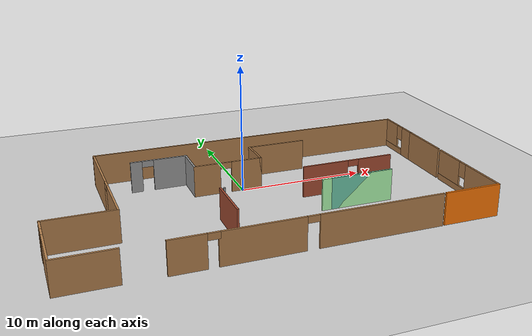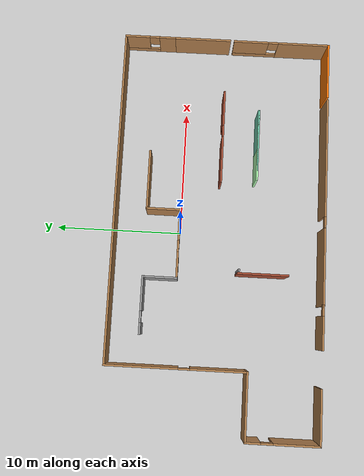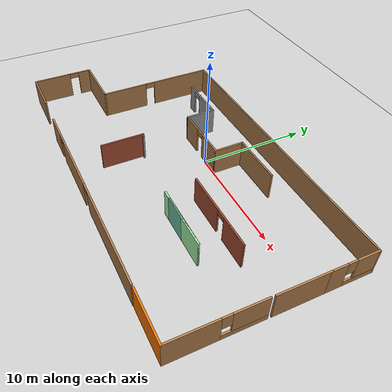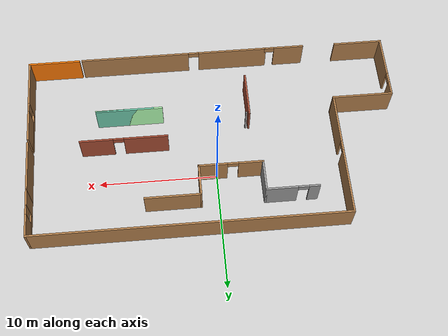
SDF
<sdf version="1.6">
 <world name="default">
  <include><uri>model://sun</uri></include>
  <include><uri>model://ground_plane</uri></include>
  <include>
   <name>floor_plan</name>
   <uri>model://floorplan</uri>
   <pose>0 -3 0 0 0 0</pose>
   <scale>1 1 1</scale>
  </include>
 </world>
</sdf>

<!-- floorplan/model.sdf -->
<sdf version='1.7'>
  <model name='floorplan'>
    <link name='Wall_1'>
      <pose>-2.93248 -1.67538 0 0 -0 0</pose>
      <self_collide>0</self_collide>
      <enable_wind>0</enable_wind>
      <kinematic>0</kinematic>
      <visual name='Wall_1_Visual'>
        <pose>0 0 1.25 0 -0 0</pose>
        <geometry>
          <box>
            <size>0.16 0.15 2.5</size>
          </box>
        </geometry>
        <material>
          <script>
            <uri>file://media/materials/scripts/gazebo.material</uri>
            <name>Gazebo/Grey</name>
          </script>
          <ambient>0 0 0 1</ambient>
          <shader type='pixel'/>
        </material>
        <meta>
          <layer>0</layer>
        </meta>
        <transparency>0</transparency>
        <cast_shadows>1</cast_shadows>
      </visual>
      <collision name='Wall_1_Collision'>
        <laser_retro>0</laser_retro>
        <max_contacts>10</max_contacts>
        <pose>0 0 1.25 0 -0 0</pose>
        <geometry>
          <box>
            <size>0.16 0.15 2.5</size>
          </box>
        </geometry>
        <surface>
          <friction>
            <ode>
              <mu>1</mu>
              <mu2>1</mu2>
              <fdir1>0 0 0</fdir1>
              <slip1>0</slip1>
              <slip2>0</slip2>
            </ode>
            <torsional>
              <coefficient>1</coefficient>
              <patch_radius>0</patch_radius>
              <surface_radius>0</surface_radius>
              <use_patch_radius>1</use_patch_radius>
              <ode>
                <slip>0</slip>
              </ode>
            </torsional>
          </friction>
          <bounce>
            <restitution_coefficient>0</restitution_coefficient>
            <threshold>1e+06</threshold>
          </bounce>
          <contact>
            <collide_without_contact>0</collide_without_contact>
            <collide_without_contact_bitmask>1</collide_without_contact_bitmask>
            <collide_bitmask>1</collide_bitmask>
            <ode>
              <soft_cfm>0</soft_cfm>
              <soft_erp>0.2</soft_erp>
              <kp>1e+13</kp>
              <kd>1</kd>
              <max_vel>0.01</max_vel>
              <min_depth>0</min_depth>
            </ode>
            <bullet>
              <split_impulse>1</split_impulse>
              <split_impulse_penetration_threshold>-0.01</split_impulse_penetration_threshold>
              <soft_cfm>0</soft_cfm>
              <soft_erp>0.2</soft_erp>
              <kp>1e+13</kp>
              <kd>1</kd>
            </bullet>
          </contact>
        </surface>
      </collision>
    </link>
    <link name='Wall_10'>
      <pose>15.7094 -4.42431 0 0 -0 1.5708</pose>
      <self_collide>0</self_collide>
      <enable_wind>0</enable_wind>
      <kinematic>0</kinematic>
      <visual name='Wall_10_Visual_0'>
        <pose>-1.80178 0 1.25 0 -0 0</pose>
        <geometry>
          <box>
            <size>4.14643 0.15 2.5</size>
          </box>
        </geometry>
        <material>
          <script>
            <uri>file://media/materials/scripts/gazebo.material</uri>
            <name>Gazebo/Wood</name>
          </script>
          <ambient>0.996078 0.47451 0.0196078 1</ambient>
          <shader type='pixel'/>
        </material>
        <meta>
          <layer>0</layer>
        </meta>
        <transparency>0</transparency>
        <cast_shadows>1</cast_shadows>
      </visual>
      <visual name='Wall_10_Visual_1'>
        <pose>2.07322 0 0.25 0 -0 0</pose>
        <geometry>
          <box>
            <size>3.60357 0.15 0.5</size>
          </box>
        </geometry>
        <material>
          <script>
            <uri>file://media/materials/scripts/gazebo.material</uri>
            <name>Gazebo/Wood</name>
          </script>
          <ambient>0.996078 0.47451 0.0196078 1</ambient>
          <shader type='pixel'/>
        </material>
        <meta>
          <layer>0</layer>
        </meta>
        <transparency>0</transparency>
        <cast_shadows>1</cast_shadows>
      </visual>
      <visual name='Wall_10_Visual_2'>
        <pose>2.47322 0 1.5 0 -0 0</pose>
        <geometry>
          <box>
            <size>2.80357 0.15 2</size>
          </box>
        </geometry>
        <material>
          <script>
            <uri>file://media/materials/scripts/gazebo.material</uri>
            <name>Gazebo/Wood</name>
          </script>
          <ambient>0.996078 0.47451 0.0196078 1</ambient>
          <shader type='pixel'/>
        </material>
        <meta>
          <layer>0</layer>
        </meta>
        <transparency>0</transparency>
        <cast_shadows>1</cast_shadows>
      </visual>
      <visual name='Wall_10_Visual_3'>
        <pose>0.671434 0 1.9 0 -0 0</pose>
        <geometry>
          <box>
            <size>0.8 0.15 1.2</size>
          </box>
        </geometry>
        <material>
          <script>
            <uri>file://media/materials/scripts/gazebo.material</uri>
            <name>Gazebo/Wood</name>
          </script>
          <ambient>0.996078 0.47451 0.0196078 1</ambient>
          <shader type='pixel'/>
        </material>
        <meta>
          <layer>0</layer>
        </meta>
        <transparency>0</transparency>
        <cast_shadows>1</cast_shadows>
      </visual>
      <collision name='Wall_10_Collision_0'>
        <laser_retro>0</laser_retro>
        <max_contacts>10</max_contacts>
        <pose>-1.80178 0 1.25 0 -0 0</pose>
        <geometry>
          <box>
            <size>4.14643 0.15 2.5</size>
          </box>
        </geometry>
        <surface>
          <friction>
            <ode>
              <mu>1</mu>
              <mu2>1</mu2>
              <fdir1>0 0 0</fdir1>
              <slip1>0</slip1>
              <slip2>0</slip2>
            </ode>
            <torsional>
              <coefficient>1</coefficient>
              <patch_radius>0</patch_radius>
              <surface_radius>0</surface_radius>
              <use_patch_radius>1</use_patch_radius>
              <ode>
                <slip>0</slip>
              </ode>
            </torsional>
          </friction>
          <bounce>
            <restitution_coefficient>0</restitution_coefficient>
            <threshold>1e+06</threshold>
          </bounce>
          <contact>
            <collide_without_contact>0</collide_without_contact>
            <collide_without_contact_bitmask>1</collide_without_contact_bitmask>
            <collide_bitmask>1</collide_bitmask>
            <ode>
              <soft_cfm>0</soft_cfm>
              <soft_erp>0.2</soft_erp>
              <kp>1e+13</kp>
              <kd>1</kd>
              <max_vel>0.01</max_vel>
              <min_depth>0</min_depth>
            </ode>
            <bullet>
              <split_impulse>1</split_impulse>
              <split_impulse_penetration_threshold>-0.01</split_impulse_penetration_threshold>
              <soft_cfm>0</soft_cfm>
              <soft_erp>0.2</soft_erp>
              <kp>1e+13</kp>
              <kd>1</kd>
            </bullet>
          </contact>
        </surface>
      </collision>
      <collision name='Wall_10_Collision_1'>
        <laser_retro>0</laser_retro>
        <max_contacts>10</max_contacts>
        <pose>2.07322 0 0.25 0 -0 0</pose>
        <geometry>
          <box>
            <size>3.60357 0.15 0.5</size>
          </box>
        </geometry>
        <surface>
          <friction>
            <ode>
              <mu>1</mu>
              <mu2>1</mu2>
              <fdir1>0 0 0</fdir1>
              <slip1>0</slip1>
              <slip2>0</slip2>
            </ode>
            <torsional>
              <coefficient>1</coefficient>
              <patch_radius>0</patch_radius>
              <surface_radius>0</surface_radius>
              <use_patch_radius>1</use_patch_radius>
              <ode>
                <slip>0</slip>
              </ode>
            </torsional>
          </friction>
          <bounce>
            <restitution_coefficient>0</restitution_coefficient>
            <threshold>1e+06</threshold>
          </bounce>
          <contact>
            <collide_without_contact>0</collide_without_contact>
            <collide_without_contact_bitmask>1</collide_without_contact_bitmask>
            <collide_bitmask>1</collide_bitmask>
            <ode>
              <soft_cfm>0</soft_cfm>
              <soft_erp>0.2</soft_erp>
              <kp>1e+13</kp>
              <kd>1</kd>
              <max_vel>0.01</max_vel>
              <min_depth>0</min_depth>
            </ode>
            <bullet>
              <split_impulse>1</split_impulse>
              <split_impulse_penetration_threshold>-0.01</split_impulse_penetration_threshold>
              <soft_cfm>0</soft_cfm>
              <soft_erp>0.2</soft_erp>
              <kp>1e+13</kp>
              <kd>1</kd>
            </bullet>
          </contact>
        </surface>
      </collision>
      <collision name='Wall_10_Collision_2'>
        <laser_retro>0</laser_retro>
        <max_contacts>10</max_contacts>
        <pose>2.47322 0 1.5 0 -0 0</pose>
        <geometry>
          <box>
            <size>2.80357 0.15 2</size>
          </box>
        </geometry>
        <surface>
          <friction>
            <ode>
              <mu>1</mu>
              <mu2>1</mu2>
              <fdir1>0 0 0</fdir1>
              <slip1>0</slip1>
              <slip2>0</slip2>
            </ode>
            <torsional>
              <coefficient>1</coefficient>
              <patch_radius>0</patch_radius>
              <surface_radius>0</surface_radius>
              <use_patch_radius>1</use_patch_radius>
              <ode>
                <slip>0</slip>
              </ode>
            </torsional>
          </friction>
          <bounce>
            <restitution_coefficient>0</restitution_coefficient>
            <threshold>1e+06</threshold>
          </bounce>
          <contact>
            <collide_without_contact>0</collide_without_contact>
            <collide_without_contact_bitmask>1</collide_without_contact_bitmask>
            <collide_bitmask>1</collide_bitmask>
            <ode>
              <soft_cfm>0</soft_cfm>
              <soft_erp>0.2</soft_erp>
              <kp>1e+13</kp>
              <kd>1</kd>
              <max_vel>0.01</max_vel>
              <min_depth>0</min_depth>
            </ode>
            <bullet>
              <split_impulse>1</split_impulse>
              <split_impulse_penetration_threshold>-0.01</split_impulse_penetration_threshold>
              <soft_cfm>0</soft_cfm>
              <soft_erp>0.2</soft_erp>
              <kp>1e+13</kp>
              <kd>1</kd>
            </bullet>
          </contact>
        </surface>
      </collision>
      <collision name='Wall_10_Collision_3'>
        <laser_retro>0</laser_retro>
        <max_contacts>10</max_contacts>
        <pose>0.671434 0 1.9 0 -0 0</pose>
        <geometry>
          <box>
            <size>0.8 0.15 1.2</size>
          </box>
        </geometry>
        <surface>
          <friction>
            <ode>
              <mu>1</mu>
              <mu2>1</mu2>
              <fdir1>0 0 0</fdir1>
              <slip1>0</slip1>
              <slip2>0</slip2>
            </ode>
            <torsional>
              <coefficient>1</coefficient>
              <patch_radius>0</patch_radius>
              <surface_radius>0</surface_radius>
              <use_patch_radius>1</use_patch_radius>
              <ode>
                <slip>0</slip>
              </ode>
            </torsional>
          </friction>
          <bounce>
            <restitution_coefficient>0</restitution_coefficient>
            <threshold>1e+06</threshold>
          </bounce>
          <contact>
            <collide_without_contact>0</collide_without_contact>
            <collide_without_contact_bitmask>1</collide_without_contact_bitmask>
            <collide_bitmask>1</collide_bitmask>
            <ode>
              <soft_cfm>0</soft_cfm>
              <soft_erp>0.2</soft_erp>
              <kp>1e+13</kp>
              <kd>1</kd>
              <max_vel>0.01</max_vel>
              <min_depth>0</min_depth>
            </ode>
            <bullet>
              <split_impulse>1</split_impulse>
              <split_impulse_penetration_threshold>-0.01</split_impulse_penetration_threshold>
              <soft_cfm>0</soft_cfm>
              <soft_erp>0.2</soft_erp>
              <kp>1e+13</kp>
              <kd>1</kd>
            </bullet>
          </contact>
        </surface>
      </collision>
    </link>
    <link name='Wall_16'>
      <pose>15.725 1.96893 0 0 -0 1.5708</pose>
      <self_collide>0</self_collide>
      <enable_wind>0</enable_wind>
      <kinematic>0</kinematic>
      <visual name='Wall_16_Visual'>
        <pose>0 0 1.25 0 -0 0</pose>
        <geometry>
          <box>
            <size>4.5 0.15 2.5</size>
          </box>
        </geometry>
        <material>
          <script>
            <uri>file://media/materials/scripts/gazebo.material</uri>
            <name>Gazebo/Wood</name>
          </script>
          <ambient>0.996078 0.47451 0.0196078 1</ambient>
          <shader type='pixel'/>
        </material>
        <meta>
          <layer>0</layer>
        </meta>
        <transparency>0</transparency>
        <cast_shadows>1</cast_shadows>
      </visual>
      <collision name='Wall_16_Collision'>
        <laser_retro>0</laser_retro>
        <max_contacts>10</max_contacts>
        <pose>0 0 1.25 0 -0 0</pose>
        <geometry>
          <box>
            <size>4.5 0.15 2.5</size>
          </box>
        </geometry>
        <surface>
          <friction>
            <ode>
              <mu>1</mu>
              <mu2>1</mu2>
              <fdir1>0 0 0</fdir1>
              <slip1>0</slip1>
              <slip2>0</slip2>
            </ode>
            <torsional>
              <coefficient>1</coefficient>
              <patch_radius>0</patch_radius>
              <surface_radius>0</surface_radius>
              <use_patch_radius>1</use_patch_radius>
              <ode>
                <slip>0</slip>
              </ode>
            </torsional>
          </friction>
          <bounce>
            <restitution_coefficient>0</restitution_coefficient>
            <threshold>1e+06</threshold>
          </bounce>
          <contact>
            <collide_without_contact>0</collide_without_contact>
            <collide_without_contact_bitmask>1</collide_without_contact_bitmask>
            <collide_bitmask>1</collide_bitmask>
            <ode>
              <soft_cfm>0</soft_cfm>
              <soft_erp>0.2</soft_erp>
              <kp>1e+13</kp>
              <kd>1</kd>
              <max_vel>0.01</max_vel>
              <min_depth>0</min_depth>
            </ode>
            <bullet>
              <split_impulse>1</split_impulse>
              <split_impulse_penetration_threshold>-0.01</split_impulse_penetration_threshold>
              <soft_cfm>0</soft_cfm>
              <soft_erp>0.2</soft_erp>
              <kp>1e+13</kp>
              <kd>1</kd>
            </bullet>
          </contact>
        </surface>
      </collision>
    </link>
    <link name='Wall_20'>
      <pose>15.725 6.19393 0 0 -0 1.5708</pose>
      <self_collide>0</self_collide>
      <enable_wind>0</enable_wind>
      <kinematic>0</kinematic>
      <visual name='Wall_20_Visual_0'>
        <pose>-1.39393 0 1.25 0 -0 0</pose>
        <geometry>
          <box>
            <size>1.46215 0.15 2.5</size>
          </box>
        </geometry>
        <material>
          <script>
            <uri>file://media/materials/scripts/gazebo.material</uri>
            <name>Gazebo/Wood</name>
          </script>
          <ambient>1 1 1 1</ambient>
          <shader type='pixel'/>
        </material>
        <meta>
          <layer>0</layer>
        </meta>
        <transparency>0</transparency>
        <cast_shadows>1</cast_shadows>
      </visual>
      <visual name='Wall_20_Visual_1'>
        <pose>0.731073 0 0.25 0 -0 0</pose>
        <geometry>
          <box>
            <size>2.78785 0.15 0.5</size>
          </box>
        </geometry>
        <material>
          <script>
            <uri>file://media/materials/scripts/gazebo.material</uri>
            <name>Gazebo/Wood</name>
          </script>
          <ambient>1 1 1 1</ambient>
          <shader type='pixel'/>
        </material>
        <meta>
          <layer>0</layer>
        </meta>
        <transparency>0</transparency>
        <cast_shadows>1</cast_shadows>
      </visual>
      <visual name='Wall_20_Visual_2'>
        <pose>1.13107 0 1.5 0 -0 0</pose>
        <geometry>
          <box>
            <size>1.98785 0.15 2</size>
          </box>
        </geometry>
        <material>
          <script>
            <uri>file://media/materials/scripts/gazebo.material</uri>
            <name>Gazebo/Wood</name>
          </script>
          <ambient>1 1 1 1</ambient>
          <shader type='pixel'/>
        </material>
        <meta>
          <layer>0</layer>
        </meta>
        <transparency>0</transparency>
        <cast_shadows>1</cast_shadows>
      </visual>
      <visual name='Wall_20_Visual_3'>
        <pose>-0.262854 0 1.9 0 -0 0</pose>
        <geometry>
          <box>
            <size>0.8 0.15 1.2</size>
          </box>
        </geometry>
        <material>
          <script>
            <uri>file://media/materials/scripts/gazebo.material</uri>
            <name>Gazebo/Wood</name>
          </script>
          <ambient>1 1 1 1</ambient>
          <shader type='pixel'/>
        </material>
        <meta>
          <layer>0</layer>
        </meta>
        <transparency>0</transparency>
        <cast_shadows>1</cast_shadows>
      </visual>
      <collision name='Wall_20_Collision_0'>
        <laser_retro>0</laser_retro>
        <max_contacts>10</max_contacts>
        <pose>-1.39393 0 1.25 0 -0 0</pose>
        <geometry>
          <box>
            <size>1.46215 0.15 2.5</size>
          </box>
        </geometry>
        <surface>
          <friction>
            <ode>
              <mu>1</mu>
              <mu2>1</mu2>
              <fdir1>0 0 0</fdir1>
              <slip1>0</slip1>
              <slip2>0</slip2>
            </ode>
            <torsional>
              <coefficient>1</coefficient>
              <patch_radius>0</patch_radius>
              <surface_radius>0</surface_radius>
              <use_patch_radius>1</use_patch_radius>
              <ode>
                <slip>0</slip>
              </ode>
            </torsional>
          </friction>
          <bounce>
            <restitution_coefficient>0</restitution_coefficient>
            <threshold>1e+06</threshold>
          </bounce>
          <contact>
            <collide_without_contact>0</collide_without_contact>
            <collide_without_contact_bitmask>1</collide_without_contact_bitmask>
            <collide_bitmask>1</collide_bitmask>
            <ode>
              <soft_cfm>0</soft_cfm>
              <soft_erp>0.2</soft_erp>
              <kp>1e+13</kp>
              <kd>1</kd>
              <max_vel>0.01</max_vel>
              <min_depth>0</min_depth>
            </ode>
            <bullet>
              <split_impulse>1</split_impulse>
              <split_impulse_penetration_threshold>-0.01</split_impulse_penetration_threshold>
              <soft_cfm>0</soft_cfm>
              <soft_erp>0.2</soft_erp>
              <kp>1e+13</kp>
              <kd>1</kd>
            </bullet>
          </contact>
        </surface>
      </collision>
      <collision name='Wall_20_Collision_1'>
        <laser_retro>0</laser_retro>
        <max_contacts>10</max_contacts>
        <pose>0.731073 0 0.25 0 -0 0</pose>
        <geometry>
          <box>
            <size>2.78785 0.15 0.5</size>
          </box>
        </geometry>
        <surface>
          <friction>
            <ode>
              <mu>1</mu>
              <mu2>1</mu2>
              <fdir1>0 0 0</fdir1>
              <slip1>0</slip1>
              <slip2>0</slip2>
            </ode>
            <torsional>
              <coefficient>1</coefficient>
              <patch_radius>0</patch_radius>
              <surface_radius>0</surface_radius>
              <use_patch_radius>1</use_patch_radius>
              <ode>
                <slip>0</slip>
              </ode>
            </torsional>
          </friction>
          <bounce>
            <restitution_coefficient>0</restitution_coefficient>
            <threshold>1e+06</threshold>
          </bounce>
          <contact>
            <collide_without_contact>0</collide_without_contact>
            <collide_without_contact_bitmask>1</collide_without_contact_bitmask>
            <collide_bitmask>1</collide_bitmask>
            <ode>
              <soft_cfm>0</soft_cfm>
              <soft_erp>0.2</soft_erp>
              <kp>1e+13</kp>
              <kd>1</kd>
              <max_vel>0.01</max_vel>
              <min_depth>0</min_depth>
            </ode>
            <bullet>
              <split_impulse>1</split_impulse>
              <split_impulse_penetration_threshold>-0.01</split_impulse_penetration_threshold>
              <soft_cfm>0</soft_cfm>
              <soft_erp>0.2</soft_erp>
              <kp>1e+13</kp>
              <kd>1</kd>
            </bullet>
          </contact>
        </surface>
      </collision>
      <collision name='Wall_20_Collision_2'>
        <laser_retro>0</laser_retro>
        <max_contacts>10</max_contacts>
        <pose>1.13107 0 1.5 0 -0 0</pose>
        <geometry>
          <box>
            <size>1.98785 0.15 2</size>
          </box>
        </geometry>
        <surface>
          <friction>
            <ode>
              <mu>1</mu>
              <mu2>1</mu2>
              <fdir1>0 0 0</fdir1>
              <slip1>0</slip1>
              <slip2>0</slip2>
            </ode>
            <torsional>
              <coefficient>1</coefficient>
              <patch_radius>0</patch_radius>
              <surface_radius>0</surface_radius>
              <use_patch_radius>1</use_patch_radius>
              <ode>
                <slip>0</slip>
              </ode>
            </torsional>
          </friction>
          <bounce>
            <restitution_coefficient>0</restitution_coefficient>
            <threshold>1e+06</threshold>
          </bounce>
          <contact>
            <collide_without_contact>0</collide_without_contact>
            <collide_without_contact_bitmask>1</collide_without_contact_bitmask>
            <collide_bitmask>1</collide_bitmask>
            <ode>
              <soft_cfm>0</soft_cfm>
              <soft_erp>0.2</soft_erp>
              <kp>1e+13</kp>
              <kd>1</kd>
              <max_vel>0.01</max_vel>
              <min_depth>0</min_depth>
            </ode>
            <bullet>
              <split_impulse>1</split_impulse>
              <split_impulse_penetration_threshold>-0.01</split_impulse_penetration_threshold>
              <soft_cfm>0</soft_cfm>
              <soft_erp>0.2</soft_erp>
              <kp>1e+13</kp>
              <kd>1</kd>
            </bullet>
          </contact>
        </surface>
      </collision>
      <collision name='Wall_20_Collision_3'>
        <laser_retro>0</laser_retro>
        <max_contacts>10</max_contacts>
        <pose>-0.262854 0 1.9 0 -0 0</pose>
        <geometry>
          <box>
            <size>0.8 0.15 1.2</size>
          </box>
        </geometry>
        <surface>
          <friction>
            <ode>
              <mu>1</mu>
              <mu2>1</mu2>
              <fdir1>0 0 0</fdir1>
              <slip1>0</slip1>
              <slip2>0</slip2>
            </ode>
            <torsional>
              <coefficient>1</coefficient>
              <patch_radius>0</patch_radius>
              <surface_radius>0</surface_radius>
              <use_patch_radius>1</use_patch_radius>
              <ode>
                <slip>0</slip>
              </ode>
            </torsional>
          </friction>
          <bounce>
            <restitution_coefficient>0</restitution_coefficient>
            <threshold>1e+06</threshold>
          </bounce>
          <contact>
            <collide_without_contact>0</collide_without_contact>
            <collide_without_contact_bitmask>1</collide_without_contact_bitmask>
            <collide_bitmask>1</collide_bitmask>
            <ode>
              <soft_cfm>0</soft_cfm>
              <soft_erp>0.2</soft_erp>
              <kp>1e+13</kp>
              <kd>1</kd>
              <max_vel>0.01</max_vel>
              <min_depth>0</min_depth>
            </ode>
            <bullet>
              <split_impulse>1</split_impulse>
              <split_impulse_penetration_threshold>-0.01</split_impulse_penetration_threshold>
              <soft_cfm>0</soft_cfm>
              <soft_erp>0.2</soft_erp>
              <kp>1e+13</kp>
              <kd>1</kd>
            </bullet>
          </contact>
        </surface>
      </collision>
    </link>
    <link name='Wall_21'>
      <pose>2.55 8.24393 0 0 -0 3.14159</pose>
      <self_collide>0</self_collide>
      <enable_wind>0</enable_wind>
      <kinematic>0</kinematic>
      <visual name='Wall_21_Visual'>
        <pose>0 0 1.25 0 -0 0</pose>
        <geometry>
          <box>
            <size>26.5 0.15 2.5</size>
          </box>
        </geometry>
        <material>
          <script>
            <uri>file://media/materials/scripts/gazebo.material</uri>
            <name>Gazebo/Wood</name>
          </script>
          <ambient>0.435294 0.796078 0.67451 1</ambient>
          <shader type='pixel'/>
        </material>
        <meta>
          <layer>0</layer>
        </meta>
        <transparency>0</transparency>
        <cast_shadows>1</cast_shadows>
      </visual>
      <collision name='Wall_21_Collision'>
        <laser_retro>0</laser_retro>
        <max_contacts>10</max_contacts>
        <pose>0 0 1.25 0 -0 0</pose>
        <geometry>
          <box>
            <size>26.5 0.15 2.5</size>
          </box>
        </geometry>
        <surface>
          <friction>
            <ode>
              <mu>1</mu>
              <mu2>1</mu2>
              <fdir1>0 0 0</fdir1>
              <slip1>0</slip1>
              <slip2>0</slip2>
            </ode>
            <torsional>
              <coefficient>1</coefficient>
              <patch_radius>0</patch_radius>
              <surface_radius>0</surface_radius>
              <use_patch_radius>1</use_patch_radius>
              <ode>
                <slip>0</slip>
              </ode>
            </torsional>
          </friction>
          <bounce>
            <restitution_coefficient>0</restitution_coefficient>
            <threshold>1e+06</threshold>
          </bounce>
          <contact>
            <collide_without_contact>0</collide_without_contact>
            <collide_without_contact_bitmask>1</collide_without_contact_bitmask>
            <collide_bitmask>1</collide_bitmask>
            <ode>
              <soft_cfm>0</soft_cfm>
              <soft_erp>0.2</soft_erp>
              <kp>1e+13</kp>
              <kd>1</kd>
              <max_vel>0.01</max_vel>
              <min_depth>0</min_depth>
            </ode>
            <bullet>
              <split_impulse>1</split_impulse>
              <split_impulse_penetration_threshold>-0.01</split_impulse_penetration_threshold>
              <soft_cfm>0</soft_cfm>
              <soft_erp>0.2</soft_erp>
              <kp>1e+13</kp>
              <kd>1</kd>
            </bullet>
          </contact>
        </surface>
      </collision>
    </link>
    <link name='Wall_22'>
      <pose>-10.625 2.81893 0 0 0 -1.5708</pose>
      <self_collide>0</self_collide>
      <enable_wind>0</enable_wind>
      <kinematic>0</kinematic>
      <visual name='Wall_22_Visual_0'>
        <pose>-2.65849 0 1.25 0 -0 0</pose>
        <geometry>
          <box>
            <size>5.68303 0.15 2.5</size>
          </box>
        </geometry>
        <material>
          <script>
            <uri>file://media/materials/scripts/gazebo.material</uri>
            <name>Gazebo/Wood</name>
          </script>
          <ambient>0.996078 0.47451 0.0196078 1</ambient>
          <shader type='pixel'/>
        </material>
        <meta>
          <layer>0</layer>
        </meta>
        <transparency>0</transparency>
        <cast_shadows>1</cast_shadows>
      </visual>
      <visual name='Wall_22_Visual_1'>
        <pose>3.29151 0 1.25 0 -0 0</pose>
        <geometry>
          <box>
            <size>4.41697 0.15 2.5</size>
          </box>
        </geometry>
        <material>
          <script>
            <uri>file://media/materials/scripts/gazebo.material</uri>
            <name>Gazebo/Wood</name>
          </script>
          <ambient>0.996078 0.47451 0.0196078 1</ambient>
          <shader type='pixel'/>
        </material>
        <meta>
          <layer>0</layer>
        </meta>
        <transparency>0</transparency>
        <cast_shadows>1</cast_shadows>
      </visual>
      <visual name='Wall_22_Visual_2'>
        <pose>0.633029 0 2.25 0 -0 0</pose>
        <geometry>
          <box>
            <size>0.9 0.15 0.5</size>
          </box>
        </geometry>
        <material>
          <script>
            <uri>file://media/materials/scripts/gazebo.material</uri>
            <name>Gazebo/Wood</name>
          </script>
          <ambient>0.996078 0.47451 0.0196078 1</ambient>
          <shader type='pixel'/>
        </material>
        <meta>
          <layer>0</layer>
        </meta>
        <transparency>0</transparency>
        <cast_shadows>1</cast_shadows>
      </visual>
      <collision name='Wall_22_Collision_0'>
        <laser_retro>0</laser_retro>
        <max_contacts>10</max_contacts>
        <pose>-2.65849 0 1.25 0 -0 0</pose>
        <geometry>
          <box>
            <size>5.68303 0.15 2.5</size>
          </box>
        </geometry>
        <surface>
          <friction>
            <ode>
              <mu>1</mu>
              <mu2>1</mu2>
              <fdir1>0 0 0</fdir1>
              <slip1>0</slip1>
              <slip2>0</slip2>
            </ode>
            <torsional>
              <coefficient>1</coefficient>
              <patch_radius>0</patch_radius>
              <surface_radius>0</surface_radius>
              <use_patch_radius>1</use_patch_radius>
              <ode>
                <slip>0</slip>
              </ode>
            </torsional>
          </friction>
          <bounce>
            <restitution_coefficient>0</restitution_coefficient>
            <threshold>1e+06</threshold>
          </bounce>
          <contact>
            <collide_without_contact>0</collide_without_contact>
            <collide_without_contact_bitmask>1</collide_without_contact_bitmask>
            <collide_bitmask>1</collide_bitmask>
            <ode>
              <soft_cfm>0</soft_cfm>
              <soft_erp>0.2</soft_erp>
              <kp>1e+13</kp>
              <kd>1</kd>
              <max_vel>0.01</max_vel>
              <min_depth>0</min_depth>
            </ode>
            <bullet>
              <split_impulse>1</split_impulse>
              <split_impulse_penetration_threshold>-0.01</split_impulse_penetration_threshold>
              <soft_cfm>0</soft_cfm>
              <soft_erp>0.2</soft_erp>
              <kp>1e+13</kp>
              <kd>1</kd>
            </bullet>
          </contact>
        </surface>
      </collision>
      <collision name='Wall_22_Collision_1'>
        <laser_retro>0</laser_retro>
        <max_contacts>10</max_contacts>
        <pose>3.29151 0 1.25 0 -0 0</pose>
        <geometry>
          <box>
            <size>4.41697 0.15 2.5</size>
          </box>
        </geometry>
        <surface>
          <friction>
            <ode>
              <mu>1</mu>
              <mu2>1</mu2>
              <fdir1>0 0 0</fdir1>
              <slip1>0</slip1>
              <slip2>0</slip2>
            </ode>
            <torsional>
              <coefficient>1</coefficient>
              <patch_radius>0</patch_radius>
              <surface_radius>0</surface_radius>
              <use_patch_radius>1</use_patch_radius>
              <ode>
                <slip>0</slip>
              </ode>
            </torsional>
          </friction>
          <bounce>
            <restitution_coefficient>0</restitution_coefficient>
            <threshold>1e+06</threshold>
          </bounce>
          <contact>
            <collide_without_contact>0</collide_without_contact>
            <collide_without_contact_bitmask>1</collide_without_contact_bitmask>
            <collide_bitmask>1</collide_bitmask>
            <ode>
              <soft_cfm>0</soft_cfm>
              <soft_erp>0.2</soft_erp>
              <kp>1e+13</kp>
              <kd>1</kd>
              <max_vel>0.01</max_vel>
              <min_depth>0</min_depth>
            </ode>
            <bullet>
              <split_impulse>1</split_impulse>
              <split_impulse_penetration_threshold>-0.01</split_impulse_penetration_threshold>
              <soft_cfm>0</soft_cfm>
              <soft_erp>0.2</soft_erp>
              <kp>1e+13</kp>
              <kd>1</kd>
            </bullet>
          </contact>
        </surface>
      </collision>
      <collision name='Wall_22_Collision_2'>
        <laser_retro>0</laser_retro>
        <max_contacts>10</max_contacts>
        <pose>0.633029 0 2.25 0 -0 0</pose>
        <geometry>
          <box>
            <size>0.9 0.15 0.5</size>
          </box>
        </geometry>
        <surface>
          <friction>
            <ode>
              <mu>1</mu>
              <mu2>1</mu2>
              <fdir1>0 0 0</fdir1>
              <slip1>0</slip1>
              <slip2>0</slip2>
            </ode>
            <torsional>
              <coefficient>1</coefficient>
              <patch_radius>0</patch_radius>
              <surface_radius>0</surface_radius>
              <use_patch_radius>1</use_patch_radius>
              <ode>
                <slip>0</slip>
              </ode>
            </torsional>
          </friction>
          <bounce>
            <restitution_coefficient>0</restitution_coefficient>
            <threshold>1e+06</threshold>
          </bounce>
          <contact>
            <collide_without_contact>0</collide_without_contact>
            <collide_without_contact_bitmask>1</collide_without_contact_bitmask>
            <collide_bitmask>1</collide_bitmask>
            <ode>
              <soft_cfm>0</soft_cfm>
              <soft_erp>0.2</soft_erp>
              <kp>1e+13</kp>
              <kd>1</kd>
              <max_vel>0.01</max_vel>
              <min_depth>0</min_depth>
            </ode>
            <bullet>
              <split_impulse>1</split_impulse>
              <split_impulse_penetration_threshold>-0.01</split_impulse_penetration_threshold>
              <soft_cfm>0</soft_cfm>
              <soft_erp>0.2</soft_erp>
              <kp>1e+13</kp>
              <kd>1</kd>
            </bullet>
          </contact>
        </surface>
      </collision>
    </link>
    <link name='Wall_23'>
      <pose>-13.175 -2.60607 0 0 -0 3.14159</pose>
      <self_collide>0</self_collide>
      <enable_wind>0</enable_wind>
      <kinematic>0</kinematic>
      <visual name='Wall_23_Visual'>
        <pose>0 0 1.25 0 -0 0</pose>
        <geometry>
          <box>
            <size>5.25 0.15 2.5</size>
          </box>
        </geometry>
        <material>
          <script>
            <uri>file://media/materials/scripts/gazebo.material</uri>
            <name>Gazebo/Wood</name>
          </script>
          <ambient>0.996078 0.47451 0.0196078 1</ambient>
          <shader type='pixel'/>
        </material>
        <meta>
          <layer>0</layer>
        </meta>
        <transparency>0</transparency>
        <cast_shadows>1</cast_shadows>
      </visual>
      <collision name='Wall_23_Collision'>
        <laser_retro>0</laser_retro>
        <max_contacts>10</max_contacts>
        <pose>0 0 1.25 0 -0 0</pose>
        <geometry>
          <box>
            <size>5.25 0.15 2.5</size>
          </box>
        </geometry>
        <surface>
          <friction>
            <ode>
              <mu>1</mu>
              <mu2>1</mu2>
              <fdir1>0 0 0</fdir1>
              <slip1>0</slip1>
              <slip2>0</slip2>
            </ode>
            <torsional>
              <coefficient>1</coefficient>
              <patch_radius>0</patch_radius>
              <surface_radius>0</surface_radius>
              <use_patch_radius>1</use_patch_radius>
              <ode>
                <slip>0</slip>
              </ode>
            </torsional>
          </friction>
          <bounce>
            <restitution_coefficient>0</restitution_coefficient>
            <threshold>1e+06</threshold>
          </bounce>
          <contact>
            <collide_without_contact>0</collide_without_contact>
            <collide_without_contact_bitmask>1</collide_without_contact_bitmask>
            <collide_bitmask>1</collide_bitmask>
            <ode>
              <soft_cfm>0</soft_cfm>
              <soft_erp>0.2</soft_erp>
              <kp>1e+13</kp>
              <kd>1</kd>
              <max_vel>0.01</max_vel>
              <min_depth>0</min_depth>
            </ode>
            <bullet>
              <split_impulse>1</split_impulse>
              <split_impulse_penetration_threshold>-0.01</split_impulse_penetration_threshold>
              <soft_cfm>0</soft_cfm>
              <soft_erp>0.2</soft_erp>
              <kp>1e+13</kp>
              <kd>1</kd>
            </bullet>
          </contact>
        </surface>
      </collision>
    </link>
    <link name='Wall_24'>
      <pose>-15.725 -5.40607 0 0 0 -1.5708</pose>
      <self_collide>0</self_collide>
      <enable_wind>0</enable_wind>
      <kinematic>0</kinematic>
      <visual name='Wall_24_Visual_1'>
        <pose>1.07666 0 1.25 0 -0 0</pose>
        <geometry>
          <box>
            <size>3.59667 0.15 2.5</size>
          </box>
        </geometry>
        <material>
          <script>
            <uri>file://media/materials/scripts/gazebo.material</uri>
            <name>Gazebo/Wood</name>
          </script>
          <ambient>0.996078 0.47451 0.0196078 1</ambient>
          <shader type='pixel'/>
        </material>
        <meta>
          <layer>0</layer>
        </meta>
        <transparency>0</transparency>
        <cast_shadows>1</cast_shadows>
      </visual>
      <visual name='Wall_24_Visual_0'>
        <pose>-2.24833 0 1.25 0 -0 0</pose>
        <geometry>
          <box>
            <size>1.25333 0.15 2.5</size>
          </box>
        </geometry>
        <material>
          <script>
            <uri>file://media/materials/scripts/gazebo.material</uri>
            <name>Gazebo/Wood</name>
          </script>
          <ambient>0.996078 0.47451 0.0196078 1</ambient>
          <shader type='pixel'/>
        </material>
        <meta>
          <layer>0</layer>
        </meta>
        <transparency>0</transparency>
        <cast_shadows>1</cast_shadows>
      </visual>
      <visual name='Wall_24_Visual_2'>
        <pose>-1.17167 0 2.25 0 -0 0</pose>
        <geometry>
          <box>
            <size>0.9 0.15 0.5</size>
          </box>
        </geometry>
        <material>
          <script>
            <uri>file://media/materials/scripts/gazebo.material</uri>
            <name>Gazebo/Wood</name>
          </script>
          <ambient>0.996078 0.47451 0.0196078 1</ambient>
          <shader type='pixel'/>
        </material>
        <meta>
          <layer>0</layer>
        </meta>
        <transparency>0</transparency>
        <cast_shadows>1</cast_shadows>
      </visual>
      <collision name='Wall_24_Collision_0'>
        <laser_retro>0</laser_retro>
        <max_contacts>10</max_contacts>
        <pose>-2.24833 0 1.25 0 -0 0</pose>
        <geometry>
          <box>
            <size>1.25333 0.15 2.5</size>
          </box>
        </geometry>
        <surface>
          <friction>
            <ode>
              <mu>1</mu>
              <mu2>1</mu2>
              <fdir1>0 0 0</fdir1>
              <slip1>0</slip1>
              <slip2>0</slip2>
            </ode>
            <torsional>
              <coefficient>1</coefficient>
              <patch_radius>0</patch_radius>
              <surface_radius>0</surface_radius>
              <use_patch_radius>1</use_patch_radius>
              <ode>
                <slip>0</slip>
              </ode>
            </torsional>
          </friction>
          <bounce>
            <restitution_coefficient>0</restitution_coefficient>
            <threshold>1e+06</threshold>
          </bounce>
          <contact>
            <collide_without_contact>0</collide_without_contact>
            <collide_without_contact_bitmask>1</collide_without_contact_bitmask>
            <collide_bitmask>1</collide_bitmask>
            <ode>
              <soft_cfm>0</soft_cfm>
              <soft_erp>0.2</soft_erp>
              <kp>1e+13</kp>
              <kd>1</kd>
              <max_vel>0.01</max_vel>
              <min_depth>0</min_depth>
            </ode>
            <bullet>
              <split_impulse>1</split_impulse>
              <split_impulse_penetration_threshold>-0.01</split_impulse_penetration_threshold>
              <soft_cfm>0</soft_cfm>
              <soft_erp>0.2</soft_erp>
              <kp>1e+13</kp>
              <kd>1</kd>
            </bullet>
          </contact>
        </surface>
      </collision>
      <collision name='Wall_24_Collision_1'>
        <laser_retro>0</laser_retro>
        <max_contacts>10</max_contacts>
        <pose>1.07666 0 1.25 0 -0 0</pose>
        <geometry>
          <box>
            <size>3.59667 0.15 2.5</size>
          </box>
        </geometry>
        <surface>
          <friction>
            <ode>
              <mu>1</mu>
              <mu2>1</mu2>
              <fdir1>0 0 0</fdir1>
              <slip1>0</slip1>
              <slip2>0</slip2>
            </ode>
            <torsional>
              <coefficient>1</coefficient>
              <patch_radius>0</patch_radius>
              <surface_radius>0</surface_radius>
              <use_patch_radius>1</use_patch_radius>
              <ode>
                <slip>0</slip>
              </ode>
            </torsional>
          </friction>
          <bounce>
            <restitution_coefficient>0</restitution_coefficient>
            <threshold>1e+06</threshold>
          </bounce>
          <contact>
            <collide_without_contact>0</collide_without_contact>
            <collide_without_contact_bitmask>1</collide_without_contact_bitmask>
            <collide_bitmask>1</collide_bitmask>
            <ode>
              <soft_cfm>0</soft_cfm>
              <soft_erp>0.2</soft_erp>
              <kp>1e+13</kp>
              <kd>1</kd>
              <max_vel>0.01</max_vel>
              <min_depth>0</min_depth>
            </ode>
            <bullet>
              <split_impulse>1</split_impulse>
              <split_impulse_penetration_threshold>-0.01</split_impulse_penetration_threshold>
              <soft_cfm>0</soft_cfm>
              <soft_erp>0.2</soft_erp>
              <kp>1e+13</kp>
              <kd>1</kd>
            </bullet>
          </contact>
        </surface>
      </collision>
      <collision name='Wall_24_Collision_2'>
        <laser_retro>0</laser_retro>
        <max_contacts>10</max_contacts>
        <pose>-1.17167 0 2.25 0 -0 0</pose>
        <geometry>
          <box>
            <size>0.9 0.15 0.5</size>
          </box>
        </geometry>
        <surface>
          <friction>
            <ode>
              <mu>1</mu>
              <mu2>1</mu2>
              <fdir1>0 0 0</fdir1>
              <slip1>0</slip1>
              <slip2>0</slip2>
            </ode>
            <torsional>
              <coefficient>1</coefficient>
              <patch_radius>0</patch_radius>
              <surface_radius>0</surface_radius>
              <use_patch_radius>1</use_patch_radius>
              <ode>
                <slip>0</slip>
              </ode>
            </torsional>
          </friction>
          <bounce>
            <restitution_coefficient>0</restitution_coefficient>
            <threshold>1e+06</threshold>
          </bounce>
          <contact>
            <collide_without_contact>0</collide_without_contact>
            <collide_without_contact_bitmask>1</collide_without_contact_bitmask>
            <collide_bitmask>1</collide_bitmask>
            <ode>
              <soft_cfm>0</soft_cfm>
              <soft_erp>0.2</soft_erp>
              <kp>1e+13</kp>
              <kd>1</kd>
              <max_vel>0.01</max_vel>
              <min_depth>0</min_depth>
            </ode>
            <bullet>
              <split_impulse>1</split_impulse>
              <split_impulse_penetration_threshold>-0.01</split_impulse_penetration_threshold>
              <soft_cfm>0</soft_cfm>
              <soft_erp>0.2</soft_erp>
              <kp>1e+13</kp>
              <kd>1</kd>
            </bullet>
          </contact>
        </surface>
      </collision>
    </link>
    <link name='Wall_26'>
      <pose>-13.675 -8.20607 0 0 -0 0</pose>
      <self_collide>0</self_collide>
      <enable_wind>0</enable_wind>
      <kinematic>0</kinematic>
      <visual name='Wall_26_Visual'>
        <pose>0 0 1.25 0 -0 0</pose>
        <geometry>
          <box>
            <size>4.25 0.15 2.5</size>
          </box>
        </geometry>
        <material>
          <script>
            <uri>file://media/materials/scripts/gazebo.material</uri>
            <name>Gazebo/Wood</name>
          </script>
          <ambient>0.996078 0.47451 0.0196078 1</ambient>
          <shader type='pixel'/>
        </material>
        <meta>
          <layer>0</layer>
        </meta>
        <transparency>0</transparency>
        <cast_shadows>1</cast_shadows>
      </visual>
      <collision name='Wall_26_Collision'>
        <laser_retro>0</laser_retro>
        <max_contacts>10</max_contacts>
        <pose>0 0 1.25 0 -0 0</pose>
        <geometry>
          <box>
            <size>4.25 0.15 2.5</size>
          </box>
        </geometry>
        <surface>
          <friction>
            <ode>
              <mu>1</mu>
              <mu2>1</mu2>
              <fdir1>0 0 0</fdir1>
              <slip1>0</slip1>
              <slip2>0</slip2>
            </ode>
            <torsional>
              <coefficient>1</coefficient>
              <patch_radius>0</patch_radius>
              <surface_radius>0</surface_radius>
              <use_patch_radius>1</use_patch_radius>
              <ode>
                <slip>0</slip>
              </ode>
            </torsional>
          </friction>
          <bounce>
            <restitution_coefficient>0</restitution_coefficient>
            <threshold>1e+06</threshold>
          </bounce>
          <contact>
            <collide_without_contact>0</collide_without_contact>
            <collide_without_contact_bitmask>1</collide_without_contact_bitmask>
            <collide_bitmask>1</collide_bitmask>
            <ode>
              <soft_cfm>0</soft_cfm>
              <soft_erp>0.2</soft_erp>
              <kp>1e+13</kp>
              <kd>1</kd>
              <max_vel>0.01</max_vel>
              <min_depth>0</min_depth>
            </ode>
            <bullet>
              <split_impulse>1</split_impulse>
              <split_impulse_penetration_threshold>-0.01</split_impulse_penetration_threshold>
              <soft_cfm>0</soft_cfm>
              <soft_erp>0.2</soft_erp>
              <kp>1e+13</kp>
              <kd>1</kd>
            </bullet>
          </contact>
        </surface>
      </collision>
    </link>
    <link name='Wall_30'>
      <pose>7.65692 0.027575 0 0 -0 0</pose>
      <self_collide>0</self_collide>
      <enable_wind>0</enable_wind>
      <kinematic>0</kinematic>
      <visual name='Wall_30_Visual_0'>
        <pose>-1.87765 0 1.25 0 -0 0</pose>
        <geometry>
          <box>
            <size>3.74469 0.15 2.5</size>
          </box>
        </geometry>
        <material>
          <script>
            <uri>file://media/materials/scripts/gazebo.material</uri>
            <name>Gazebo/Bricks</name>
          </script>
          <ambient>1 1 1 1</ambient>
          <shader type='pixel'/>
        </material>
        <meta>
          <layer>0</layer>
        </meta>
        <transparency>0</transparency>
        <cast_shadows>1</cast_shadows>
      </visual>
      <visual name='Wall_30_Visual_1'>
        <pose>2.32235 0 1.25 0 -0 0</pose>
        <geometry>
          <box>
            <size>2.85531 0.15 2.5</size>
          </box>
        </geometry>
        <material>
          <script>
            <uri>file://media/materials/scripts/gazebo.material</uri>
            <name>Gazebo/Bricks</name>
          </script>
          <ambient>1 1 1 1</ambient>
          <shader type='pixel'/>
        </material>
        <meta>
          <layer>0</layer>
        </meta>
        <transparency>0</transparency>
        <cast_shadows>1</cast_shadows>
      </visual>
      <visual name='Wall_30_Visual_2'>
        <pose>0.444693 0 2.25 0 -0 0</pose>
        <geometry>
          <box>
            <size>0.9 0.15 0.5</size>
          </box>
        </geometry>
        <material>
          <script>
            <uri>file://media/materials/scripts/gazebo.material</uri>
            <name>Gazebo/Bricks</name>
          </script>
          <ambient>1 1 1 1</ambient>
          <shader type='pixel'/>
        </material>
        <meta>
          <layer>0</layer>
        </meta>
        <transparency>0</transparency>
        <cast_shadows>1</cast_shadows>
      </visual>
      <collision name='Wall_30_Collision_0'>
        <laser_retro>0</laser_retro>
        <max_contacts>10</max_contacts>
        <pose>-1.87765 0 1.25 0 -0 0</pose>
        <geometry>
          <box>
            <size>3.74469 0.15 2.5</size>
          </box>
        </geometry>
        <surface>
          <friction>
            <ode>
              <mu>1</mu>
              <mu2>1</mu2>
              <fdir1>0 0 0</fdir1>
              <slip1>0</slip1>
              <slip2>0</slip2>
            </ode>
            <torsional>
              <coefficient>1</coefficient>
              <patch_radius>0</patch_radius>
              <surface_radius>0</surface_radius>
              <use_patch_radius>1</use_patch_radius>
              <ode>
                <slip>0</slip>
              </ode>
            </torsional>
          </friction>
          <bounce>
            <restitution_coefficient>0</restitution_coefficient>
            <threshold>1e+06</threshold>
          </bounce>
          <contact>
            <collide_without_contact>0</collide_without_contact>
            <collide_without_contact_bitmask>1</collide_without_contact_bitmask>
            <collide_bitmask>1</collide_bitmask>
            <ode>
              <soft_cfm>0</soft_cfm>
              <soft_erp>0.2</soft_erp>
              <kp>1e+13</kp>
              <kd>1</kd>
              <max_vel>0.01</max_vel>
              <min_depth>0</min_depth>
            </ode>
            <bullet>
              <split_impulse>1</split_impulse>
              <split_impulse_penetration_threshold>-0.01</split_impulse_penetration_threshold>
              <soft_cfm>0</soft_cfm>
              <soft_erp>0.2</soft_erp>
              <kp>1e+13</kp>
              <kd>1</kd>
            </bullet>
          </contact>
        </surface>
      </collision>
      <collision name='Wall_30_Collision_1'>
        <laser_retro>0</laser_retro>
        <max_contacts>10</max_contacts>
        <pose>2.32235 0 1.25 0 -0 0</pose>
        <geometry>
          <box>
            <size>2.85531 0.15 2.5</size>
          </box>
        </geometry>
        <surface>
          <friction>
            <ode>
              <mu>1</mu>
              <mu2>1</mu2>
              <fdir1>0 0 0</fdir1>
              <slip1>0</slip1>
              <slip2>0</slip2>
            </ode>
            <torsional>
              <coefficient>1</coefficient>
              <patch_radius>0</patch_radius>
              <surface_radius>0</surface_radius>
              <use_patch_radius>1</use_patch_radius>
              <ode>
                <slip>0</slip>
              </ode>
            </torsional>
          </friction>
          <bounce>
            <restitution_coefficient>0</restitution_coefficient>
            <threshold>1e+06</threshold>
          </bounce>
          <contact>
            <collide_without_contact>0</collide_without_contact>
            <collide_without_contact_bitmask>1</collide_without_contact_bitmask>
            <collide_bitmask>1</collide_bitmask>
            <ode>
              <soft_cfm>0</soft_cfm>
              <soft_erp>0.2</soft_erp>
              <kp>1e+13</kp>
              <kd>1</kd>
              <max_vel>0.01</max_vel>
              <min_depth>0</min_depth>
            </ode>
            <bullet>
              <split_impulse>1</split_impulse>
              <split_impulse_penetration_threshold>-0.01</split_impulse_penetration_threshold>
              <soft_cfm>0</soft_cfm>
              <soft_erp>0.2</soft_erp>
              <kp>1e+13</kp>
              <kd>1</kd>
            </bullet>
          </contact>
        </surface>
      </collision>
      <collision name='Wall_30_Collision_2'>
        <laser_retro>0</laser_retro>
        <max_contacts>10</max_contacts>
        <pose>0.444693 0 2.25 0 -0 0</pose>
        <geometry>
          <box>
            <size>0.9 0.15 0.5</size>
          </box>
        </geometry>
        <surface>
          <friction>
            <ode>
              <mu>1</mu>
              <mu2>1</mu2>
              <fdir1>0 0 0</fdir1>
              <slip1>0</slip1>
              <slip2>0</slip2>
            </ode>
            <torsional>
              <coefficient>1</coefficient>
              <patch_radius>0</patch_radius>
              <surface_radius>0</surface_radius>
              <use_patch_radius>1</use_patch_radius>
              <ode>
                <slip>0</slip>
              </ode>
            </torsional>
          </friction>
          <bounce>
            <restitution_coefficient>0</restitution_coefficient>
            <threshold>1e+06</threshold>
          </bounce>
          <contact>
            <collide_without_contact>0</collide_without_contact>
            <collide_without_contact_bitmask>1</collide_without_contact_bitmask>
            <collide_bitmask>1</collide_bitmask>
            <ode>
              <soft_cfm>0</soft_cfm>
              <soft_erp>0.2</soft_erp>
              <kp>1e+13</kp>
              <kd>1</kd>
              <max_vel>0.01</max_vel>
              <min_depth>0</min_depth>
            </ode>
            <bullet>
              <split_impulse>1</split_impulse>
              <split_impulse_penetration_threshold>-0.01</split_impulse_penetration_threshold>
              <soft_cfm>0</soft_cfm>
              <soft_erp>0.2</soft_erp>
              <kp>1e+13</kp>
              <kd>1</kd>
            </bullet>
          </contact>
        </surface>
      </collision>
    </link>
    <link name='Wall_32'>
      <pose>-5.98815 5.71707 0 0 -0 0</pose>
      <self_collide>0</self_collide>
      <enable_wind>0</enable_wind>
      <kinematic>0</kinematic>
      <visual name='Wall_32_Visual_0'>
        <pose>-1.79547 0 1.25 0 -0 0</pose>
        <geometry>
          <box>
            <size>0.90906 0.15 2.5</size>
          </box>
        </geometry>
        <material>
          <script>
            <uri>file://media/materials/scripts/gazebo.material</uri>
            <name>Gazebo/Grey</name>
          </script>
          <ambient>1 1 1 1</ambient>
          <shader type='pixel'/>
        </material>
        <meta>
          <layer>0</layer>
        </meta>
        <transparency>0</transparency>
        <cast_shadows>1</cast_shadows>
      </visual>
      <visual name='Wall_32_Visual_1'>
        <pose>0.90453 0 1.25 0 -0 0</pose>
        <geometry>
          <box>
            <size>2.69094 0.15 2.5</size>
          </box>
        </geometry>
        <material>
          <script>
            <uri>file://media/materials/scripts/gazebo.material</uri>
            <name>Gazebo/Grey</name>
          </script>
          <ambient>1 1 1 1</ambient>
          <shader type='pixel'/>
        </material>
        <meta>
          <layer>0</layer>
        </meta>
        <transparency>0</transparency>
        <cast_shadows>1</cast_shadows>
      </visual>
      <visual name='Wall_32_Visual_2'>
        <pose>-0.89094 0 2.25 0 -0 0</pose>
        <geometry>
          <box>
            <size>0.9 0.15 0.5</size>
          </box>
        </geometry>
        <material>
          <script>
            <uri>file://media/materials/scripts/gazebo.material</uri>
            <name>Gazebo/Grey</name>
          </script>
          <ambient>1 1 1 1</ambient>
          <shader type='pixel'/>
        </material>
        <meta>
          <layer>0</layer>
        </meta>
        <transparency>0</transparency>
        <cast_shadows>1</cast_shadows>
      </visual>
      <collision name='Wall_32_Collision_0'>
        <laser_retro>0</laser_retro>
        <max_contacts>10</max_contacts>
        <pose>-1.79547 0 1.25 0 -0 0</pose>
        <geometry>
          <box>
            <size>0.90906 0.15 2.5</size>
          </box>
        </geometry>
        <surface>
          <friction>
            <ode>
              <mu>1</mu>
              <mu2>1</mu2>
              <fdir1>0 0 0</fdir1>
              <slip1>0</slip1>
              <slip2>0</slip2>
            </ode>
            <torsional>
              <coefficient>1</coefficient>
              <patch_radius>0</patch_radius>
              <surface_radius>0</surface_radius>
              <use_patch_radius>1</use_patch_radius>
              <ode>
                <slip>0</slip>
              </ode>
            </torsional>
          </friction>
          <bounce>
            <restitution_coefficient>0</restitution_coefficient>
            <threshold>1e+06</threshold>
          </bounce>
          <contact>
            <collide_without_contact>0</collide_without_contact>
            <collide_without_contact_bitmask>1</collide_without_contact_bitmask>
            <collide_bitmask>1</collide_bitmask>
            <ode>
              <soft_cfm>0</soft_cfm>
              <soft_erp>0.2</soft_erp>
              <kp>1e+13</kp>
              <kd>1</kd>
              <max_vel>0.01</max_vel>
              <min_depth>0</min_depth>
            </ode>
            <bullet>
              <split_impulse>1</split_impulse>
              <split_impulse_penetration_threshold>-0.01</split_impulse_penetration_threshold>
              <soft_cfm>0</soft_cfm>
              <soft_erp>0.2</soft_erp>
              <kp>1e+13</kp>
              <kd>1</kd>
            </bullet>
          </contact>
        </surface>
      </collision>
      <collision name='Wall_32_Collision_1'>
        <laser_retro>0</laser_retro>
        <max_contacts>10</max_contacts>
        <pose>0.90453 0 1.25 0 -0 0</pose>
        <geometry>
          <box>
            <size>2.69094 0.15 2.5</size>
          </box>
        </geometry>
        <surface>
          <friction>
            <ode>
              <mu>1</mu>
              <mu2>1</mu2>
              <fdir1>0 0 0</fdir1>
              <slip1>0</slip1>
              <slip2>0</slip2>
            </ode>
            <torsional>
              <coefficient>1</coefficient>
              <patch_radius>0</patch_radius>
              <surface_radius>0</surface_radius>
              <use_patch_radius>1</use_patch_radius>
              <ode>
                <slip>0</slip>
              </ode>
            </torsional>
          </friction>
          <bounce>
            <restitution_coefficient>0</restitution_coefficient>
            <threshold>1e+06</threshold>
          </bounce>
          <contact>
            <collide_without_contact>0</collide_without_contact>
            <collide_without_contact_bitmask>1</collide_without_contact_bitmask>
            <collide_bitmask>1</collide_bitmask>
            <ode>
              <soft_cfm>0</soft_cfm>
              <soft_erp>0.2</soft_erp>
              <kp>1e+13</kp>
              <kd>1</kd>
              <max_vel>0.01</max_vel>
              <min_depth>0</min_depth>
            </ode>
            <bullet>
              <split_impulse>1</split_impulse>
              <split_impulse_penetration_threshold>-0.01</split_impulse_penetration_threshold>
              <soft_cfm>0</soft_cfm>
              <soft_erp>0.2</soft_erp>
              <kp>1e+13</kp>
              <kd>1</kd>
            </bullet>
          </contact>
        </surface>
      </collision>
      <collision name='Wall_32_Collision_2'>
        <laser_retro>0</laser_retro>
        <max_contacts>10</max_contacts>
        <pose>-0.89094 0 2.25 0 -0 0</pose>
        <geometry>
          <box>
            <size>0.9 0.15 0.5</size>
          </box>
        </geometry>
        <surface>
          <friction>
            <ode>
              <mu>1</mu>
              <mu2>1</mu2>
              <fdir1>0 0 0</fdir1>
              <slip1>0</slip1>
              <slip2>0</slip2>
            </ode>
            <torsional>
              <coefficient>1</coefficient>
              <patch_radius>0</patch_radius>
              <surface_radius>0</surface_radius>
              <use_patch_radius>1</use_patch_radius>
              <ode>
                <slip>0</slip>
              </ode>
            </torsional>
          </friction>
          <bounce>
            <restitution_coefficient>0</restitution_coefficient>
            <threshold>1e+06</threshold>
          </bounce>
          <contact>
            <collide_without_contact>0</collide_without_contact>
            <collide_without_contact_bitmask>1</collide_without_contact_bitmask>
            <collide_bitmask>1</collide_bitmask>
            <ode>
              <soft_cfm>0</soft_cfm>
              <soft_erp>0.2</soft_erp>
              <kp>1e+13</kp>
              <kd>1</kd>
              <max_vel>0.01</max_vel>
              <min_depth>0</min_depth>
            </ode>
            <bullet>
              <split_impulse>1</split_impulse>
              <split_impulse_penetration_threshold>-0.01</split_impulse_penetration_threshold>
              <soft_cfm>0</soft_cfm>
              <soft_erp>0.2</soft_erp>
              <kp>1e+13</kp>
              <kd>1</kd>
            </bullet>
          </contact>
        </surface>
      </collision>
    </link>
    <link name='Wall_33'>
      <pose>-3.81315 4.41707 0 0 0 -1.5708</pose>
      <self_collide>0</self_collide>
      <enable_wind>0</enable_wind>
      <kinematic>0</kinematic>
      <visual name='Wall_33_Visual'>
        <pose>0 0 1.25 0 -0 0</pose>
        <geometry>
          <box>
            <size>2.75 0.15 2.5</size>
          </box>
        </geometry>
        <material>
          <script>
            <uri>file://media/materials/scripts/gazebo.material</uri>
            <name>Gazebo/Grey</name>
          </script>
          <ambient>1 1 1 1</ambient>
          <shader type='pixel'/>
        </material>
        <meta>
          <layer>0</layer>
        </meta>
        <transparency>0</transparency>
        <cast_shadows>1</cast_shadows>
      </visual>
      <collision name='Wall_33_Collision'>
        <laser_retro>0</laser_retro>
        <max_contacts>10</max_contacts>
        <pose>0 0 1.25 0 -0 0</pose>
        <geometry>
          <box>
            <size>2.75 0.15 2.5</size>
          </box>
        </geometry>
        <surface>
          <friction>
            <ode>
              <mu>1</mu>
              <mu2>1</mu2>
              <fdir1>0 0 0</fdir1>
              <slip1>0</slip1>
              <slip2>0</slip2>
            </ode>
            <torsional>
              <coefficient>1</coefficient>
              <patch_radius>0</patch_radius>
              <surface_radius>0</surface_radius>
              <use_patch_radius>1</use_patch_radius>
              <ode>
                <slip>0</slip>
              </ode>
            </torsional>
          </friction>
          <bounce>
            <restitution_coefficient>0</restitution_coefficient>
            <threshold>1e+06</threshold>
          </bounce>
          <contact>
            <collide_without_contact>0</collide_without_contact>
            <collide_without_contact_bitmask>1</collide_without_contact_bitmask>
            <collide_bitmask>1</collide_bitmask>
            <ode>
              <soft_cfm>0</soft_cfm>
              <soft_erp>0.2</soft_erp>
              <kp>1e+13</kp>
              <kd>1</kd>
              <max_vel>0.01</max_vel>
              <min_depth>0</min_depth>
            </ode>
            <bullet>
              <split_impulse>1</split_impulse>
              <split_impulse_penetration_threshold>-0.01</split_impulse_penetration_threshold>
              <soft_cfm>0</soft_cfm>
              <soft_erp>0.2</soft_erp>
              <kp>1e+13</kp>
              <kd>1</kd>
            </bullet>
          </contact>
        </surface>
      </collision>
    </link>
    <link name='Wall_34'>
      <pose>-1.13815 3.11707 0 0 -0 0</pose>
      <self_collide>0</self_collide>
      <enable_wind>0</enable_wind>
      <kinematic>0</kinematic>
      <visual name='Wall_34_Visual_0'>
        <pose>-1.68834 0 1.25 0 -0 0</pose>
        <geometry>
          <box>
            <size>2.12332 0.15 2.5</size>
          </box>
        </geometry>
        <material>
          <script>
            <uri>file://media/materials/scripts/gazebo.material</uri>
            <name>Gazebo/Wood</name>
          </script>
          <ambient>1 1 1 1</ambient>
          <shader type='pixel'/>
        </material>
        <meta>
          <layer>0</layer>
        </meta>
        <transparency>0</transparency>
        <cast_shadows>1</cast_shadows>
      </visual>
      <visual name='Wall_34_Visual_1'>
        <pose>1.51166 0 1.25 0 -0 0</pose>
        <geometry>
          <box>
            <size>2.47668 0.15 2.5</size>
          </box>
        </geometry>
        <material>
          <script>
            <uri>file://media/materials/scripts/gazebo.material</uri>
            <name>Gazebo/Wood</name>
          </script>
          <ambient>1 1 1 1</ambient>
          <shader type='pixel'/>
        </material>
        <meta>
          <layer>0</layer>
        </meta>
        <transparency>0</transparency>
        <cast_shadows>1</cast_shadows>
      </visual>
      <visual name='Wall_34_Visual_2'>
        <pose>-0.17668 0 2.25 0 -0 0</pose>
        <geometry>
          <box>
            <size>0.9 0.15 0.5</size>
          </box>
        </geometry>
        <material>
          <script>
            <uri>file://media/materials/scripts/gazebo.material</uri>
            <name>Gazebo/Wood</name>
          </script>
          <ambient>1 1 1 1</ambient>
          <shader type='pixel'/>
        </material>
        <meta>
          <layer>0</layer>
        </meta>
        <transparency>0</transparency>
        <cast_shadows>1</cast_shadows>
      </visual>
      <collision name='Wall_34_Collision_0'>
        <laser_retro>0</laser_retro>
        <max_contacts>10</max_contacts>
        <pose>-1.68834 0 1.25 0 -0 0</pose>
        <geometry>
          <box>
            <size>2.12332 0.15 2.5</size>
          </box>
        </geometry>
        <surface>
          <friction>
            <ode>
              <mu>1</mu>
              <mu2>1</mu2>
              <fdir1>0 0 0</fdir1>
              <slip1>0</slip1>
              <slip2>0</slip2>
            </ode>
            <torsional>
              <coefficient>1</coefficient>
              <patch_radius>0</patch_radius>
              <surface_radius>0</surface_radius>
              <use_patch_radius>1</use_patch_radius>
              <ode>
                <slip>0</slip>
              </ode>
            </torsional>
          </friction>
          <bounce>
            <restitution_coefficient>0</restitution_coefficient>
            <threshold>1e+06</threshold>
          </bounce>
          <contact>
            <collide_without_contact>0</collide_without_contact>
            <collide_without_contact_bitmask>1</collide_without_contact_bitmask>
            <collide_bitmask>1</collide_bitmask>
            <ode>
              <soft_cfm>0</soft_cfm>
              <soft_erp>0.2</soft_erp>
              <kp>1e+13</kp>
              <kd>1</kd>
              <max_vel>0.01</max_vel>
              <min_depth>0</min_depth>
            </ode>
            <bullet>
              <split_impulse>1</split_impulse>
              <split_impulse_penetration_threshold>-0.01</split_impulse_penetration_threshold>
              <soft_cfm>0</soft_cfm>
              <soft_erp>0.2</soft_erp>
              <kp>1e+13</kp>
              <kd>1</kd>
            </bullet>
          </contact>
        </surface>
      </collision>
      <collision name='Wall_34_Collision_1'>
        <laser_retro>0</laser_retro>
        <max_contacts>10</max_contacts>
        <pose>1.51166 0 1.25 0 -0 0</pose>
        <geometry>
          <box>
            <size>2.47668 0.15 2.5</size>
          </box>
        </geometry>
        <surface>
          <friction>
            <ode>
              <mu>1</mu>
              <mu2>1</mu2>
              <fdir1>0 0 0</fdir1>
              <slip1>0</slip1>
              <slip2>0</slip2>
            </ode>
            <torsional>
              <coefficient>1</coefficient>
              <patch_radius>0</patch_radius>
              <surface_radius>0</surface_radius>
              <use_patch_radius>1</use_patch_radius>
              <ode>
                <slip>0</slip>
              </ode>
            </torsional>
          </friction>
          <bounce>
            <restitution_coefficient>0</restitution_coefficient>
            <threshold>1e+06</threshold>
          </bounce>
          <contact>
            <collide_without_contact>0</collide_without_contact>
            <collide_without_contact_bitmask>1</collide_without_contact_bitmask>
            <collide_bitmask>1</collide_bitmask>
            <ode>
              <soft_cfm>0</soft_cfm>
              <soft_erp>0.2</soft_erp>
              <kp>1e+13</kp>
              <kd>1</kd>
              <max_vel>0.01</max_vel>
              <min_depth>0</min_depth>
            </ode>
            <bullet>
              <split_impulse>1</split_impulse>
              <split_impulse_penetration_threshold>-0.01</split_impulse_penetration_threshold>
              <soft_cfm>0</soft_cfm>
              <soft_erp>0.2</soft_erp>
              <kp>1e+13</kp>
              <kd>1</kd>
            </bullet>
          </contact>
        </surface>
      </collision>
      <collision name='Wall_34_Collision_2'>
        <laser_retro>0</laser_retro>
        <max_contacts>10</max_contacts>
        <pose>-0.17668 0 2.25 0 -0 0</pose>
        <geometry>
          <box>
            <size>0.9 0.15 0.5</size>
          </box>
        </geometry>
        <surface>
          <friction>
            <ode>
              <mu>1</mu>
              <mu2>1</mu2>
              <fdir1>0 0 0</fdir1>
              <slip1>0</slip1>
              <slip2>0</slip2>
            </ode>
            <torsional>
              <coefficient>1</coefficient>
              <patch_radius>0</patch_radius>
              <surface_radius>0</surface_radius>
              <use_patch_radius>1</use_patch_radius>
              <ode>
                <slip>0</slip>
              </ode>
            </torsional>
          </friction>
          <bounce>
            <restitution_coefficient>0</restitution_coefficient>
            <threshold>1e+06</threshold>
          </bounce>
          <contact>
            <collide_without_contact>0</collide_without_contact>
            <collide_without_contact_bitmask>1</collide_without_contact_bitmask>
            <collide_bitmask>1</collide_bitmask>
            <ode>
              <soft_cfm>0</soft_cfm>
              <soft_erp>0.2</soft_erp>
              <kp>1e+13</kp>
              <kd>1</kd>
              <max_vel>0.01</max_vel>
              <min_depth>0</min_depth>
            </ode>
            <bullet>
              <split_impulse>1</split_impulse>
              <split_impulse_penetration_threshold>-0.01</split_impulse_penetration_threshold>
              <soft_cfm>0</soft_cfm>
              <soft_erp>0.2</soft_erp>
              <kp>1e+13</kp>
              <kd>1</kd>
            </bullet>
          </contact>
        </surface>
      </collision>
    </link>
    <link name='Wall_35'>
      <pose>1.53685 4.41707 0 0 -0 1.5708</pose>
      <self_collide>0</self_collide>
      <enable_wind>0</enable_wind>
      <kinematic>0</kinematic>
      <visual name='Wall_35_Visual'>
        <pose>0 0 1.25 0 -0 0</pose>
        <geometry>
          <box>
            <size>2.75 0.15 2.5</size>
          </box>
        </geometry>
        <material>
          <script>
            <uri>file://media/materials/scripts/gazebo.material</uri>
            <name>Gazebo/Wood</name>
          </script>
          <ambient>1 1 1 1</ambient>
          <shader type='pixel'/>
        </material>
        <meta>
          <layer>0</layer>
        </meta>
        <transparency>0</transparency>
        <cast_shadows>1</cast_shadows>
      </visual>
      <collision name='Wall_35_Collision'>
        <laser_retro>0</laser_retro>
        <max_contacts>10</max_contacts>
        <pose>0 0 1.25 0 -0 0</pose>
        <geometry>
          <box>
            <size>2.75 0.15 2.5</size>
          </box>
        </geometry>
        <surface>
          <friction>
            <ode>
              <mu>1</mu>
              <mu2>1</mu2>
              <fdir1>0 0 0</fdir1>
              <slip1>0</slip1>
              <slip2>0</slip2>
            </ode>
            <torsional>
              <coefficient>1</coefficient>
              <patch_radius>0</patch_radius>
              <surface_radius>0</surface_radius>
              <use_patch_radius>1</use_patch_radius>
              <ode>
                <slip>0</slip>
              </ode>
            </torsional>
          </friction>
          <bounce>
            <restitution_coefficient>0</restitution_coefficient>
            <threshold>1e+06</threshold>
          </bounce>
          <contact>
            <collide_without_contact>0</collide_without_contact>
            <collide_without_contact_bitmask>1</collide_without_contact_bitmask>
            <collide_bitmask>1</collide_bitmask>
            <ode>
              <soft_cfm>0</soft_cfm>
              <soft_erp>0.2</soft_erp>
              <kp>1e+13</kp>
              <kd>1</kd>
              <max_vel>0.01</max_vel>
              <min_depth>0</min_depth>
            </ode>
            <bullet>
              <split_impulse>1</split_impulse>
              <split_impulse_penetration_threshold>-0.01</split_impulse_penetration_threshold>
              <soft_cfm>0</soft_cfm>
              <soft_erp>0.2</soft_erp>
              <kp>1e+13</kp>
              <kd>1</kd>
            </bullet>
          </contact>
        </surface>
      </collision>
    </link>
    <link name='Wall_36'>
      <pose>3.83685 5.71707 0 0 -0 0</pose>
      <self_collide>0</self_collide>
      <enable_wind>0</enable_wind>
      <kinematic>0</kinematic>
      <visual name='Wall_36_Visual'>
        <pose>0 0 1.25 0 -0 0</pose>
        <geometry>
          <box>
            <size>4.75 0.15 2.5</size>
          </box>
        </geometry>
        <material>
          <script>
            <uri>file://media/materials/scripts/gazebo.material</uri>
            <name>Gazebo/Wood</name>
          </script>
          <ambient>1 1 1 1</ambient>
          <shader type='pixel'/>
        </material>
        <meta>
          <layer>0</layer>
        </meta>
        <transparency>0</transparency>
        <cast_shadows>1</cast_shadows>
      </visual>
      <collision name='Wall_36_Collision'>
        <laser_retro>0</laser_retro>
        <max_contacts>10</max_contacts>
        <pose>0 0 1.25 0 -0 0</pose>
        <geometry>
          <box>
            <size>4.75 0.15 2.5</size>
          </box>
        </geometry>
        <surface>
          <friction>
            <ode>
              <mu>1</mu>
              <mu2>1</mu2>
              <fdir1>0 0 0</fdir1>
              <slip1>0</slip1>
              <slip2>0</slip2>
            </ode>
            <torsional>
              <coefficient>1</coefficient>
              <patch_radius>0</patch_radius>
              <surface_radius>0</surface_radius>
              <use_patch_radius>1</use_patch_radius>
              <ode>
                <slip>0</slip>
              </ode>
            </torsional>
          </friction>
          <bounce>
            <restitution_coefficient>0</restitution_coefficient>
            <threshold>1e+06</threshold>
          </bounce>
          <contact>
            <collide_without_contact>0</collide_without_contact>
            <collide_without_contact_bitmask>1</collide_without_contact_bitmask>
            <collide_bitmask>1</collide_bitmask>
            <ode>
              <soft_cfm>0</soft_cfm>
              <soft_erp>0.2</soft_erp>
              <kp>1e+13</kp>
              <kd>1</kd>
              <max_vel>0.01</max_vel>
              <min_depth>0</min_depth>
            </ode>
            <bullet>
              <split_impulse>1</split_impulse>
              <split_impulse_penetration_threshold>-0.01</split_impulse_penetration_threshold>
              <soft_cfm>0</soft_cfm>
              <soft_erp>0.2</soft_erp>
              <kp>1e+13</kp>
              <kd>1</kd>
            </bullet>
          </contact>
        </surface>
      </collision>
    </link>
    <link name='Wall_38'>
      <pose>-3.18742 -3.53777 0 0 0 -1.5708</pose>
      <self_collide>0</self_collide>
      <enable_wind>0</enable_wind>
      <kinematic>0</kinematic>
      <visual name='Wall_38_Visual'>
        <pose>0 0 1.25 0 -0 0</pose>
        <geometry>
          <box>
            <size>4 0.15 2.5</size>
          </box>
        </geometry>
        <material>
          <script>
            <uri>file://media/materials/scripts/gazebo.material</uri>
            <name>Gazebo/Bricks</name>
          </script>
          <ambient>1 1 1 1</ambient>
          <shader type='pixel'/>
        </material>
        <meta>
          <layer>0</layer>
        </meta>
        <transparency>0</transparency>
        <cast_shadows>1</cast_shadows>
      </visual>
      <collision name='Wall_38_Collision'>
        <laser_retro>0</laser_retro>
        <max_contacts>10</max_contacts>
        <pose>0 0 1.25 0 -0 0</pose>
        <geometry>
          <box>
            <size>4 0.15 2.5</size>
          </box>
        </geometry>
        <surface>
          <friction>
            <ode>
              <mu>1</mu>
              <mu2>1</mu2>
              <fdir1>0 0 0</fdir1>
              <slip1>0</slip1>
              <slip2>0</slip2>
            </ode>
            <torsional>
              <coefficient>1</coefficient>
              <patch_radius>0</patch_radius>
              <surface_radius>0</surface_radius>
              <use_patch_radius>1</use_patch_radius>
              <ode>
                <slip>0</slip>
              </ode>
            </torsional>
          </friction>
          <bounce>
            <restitution_coefficient>0</restitution_coefficient>
            <threshold>1e+06</threshold>
          </bounce>
          <contact>
            <collide_without_contact>0</collide_without_contact>
            <collide_without_contact_bitmask>1</collide_without_contact_bitmask>
            <collide_bitmask>1</collide_bitmask>
            <ode>
              <soft_cfm>0</soft_cfm>
              <soft_erp>0.2</soft_erp>
              <kp>1e+13</kp>
              <kd>1</kd>
              <max_vel>0.01</max_vel>
              <min_depth>0</min_depth>
            </ode>
            <bullet>
              <split_impulse>1</split_impulse>
              <split_impulse_penetration_threshold>-0.01</split_impulse_penetration_threshold>
              <soft_cfm>0</soft_cfm>
              <soft_erp>0.2</soft_erp>
              <kp>1e+13</kp>
              <kd>1</kd>
            </bullet>
          </contact>
        </surface>
      </collision>
    </link>
    <link name='Wall_42'>
      <pose>7.47697 -2.78983 0 0 -0 0</pose>
      <self_collide>0</self_collide>
      <enable_wind>0</enable_wind>
      <kinematic>0</kinematic>
      <visual name='Wall_42_Visual'>
        <pose>0 0 1.25 0 -0 0</pose>
        <geometry>
          <box>
            <size>5 0.15 2.5</size>
          </box>
        </geometry>
        <material>
          <script>
            <uri>file://media/materials/scripts/gazebo.material</uri>
            <name>Gazebo/Grey</name>
          </script>
          <ambient>0.435294 0.796078 0.67451 1</ambient>
          <shader type='pixel'/>
        </material>
        <meta>
          <layer>0</layer>
        </meta>
        <transparency>0</transparency>
        <cast_shadows>1</cast_shadows>
      </visual>
      <collision name='Wall_42_Collision'>
        <laser_retro>0</laser_retro>
        <max_contacts>10</max_contacts>
        <pose>0 0 1.25 0 -0 0</pose>
        <geometry>
          <box>
            <size>5 0.15 2.5</size>
          </box>
        </geometry>
        <surface>
          <friction>
            <ode>
              <mu>1</mu>
              <mu2>1</mu2>
              <fdir1>0 0 0</fdir1>
              <slip1>0</slip1>
              <slip2>0</slip2>
            </ode>
            <torsional>
              <coefficient>1</coefficient>
              <patch_radius>0</patch_radius>
              <surface_radius>0</surface_radius>
              <use_patch_radius>1</use_patch_radius>
              <ode>
                <slip>0</slip>
              </ode>
            </torsional>
          </friction>
          <bounce>
            <restitution_coefficient>0</restitution_coefficient>
            <threshold>1e+06</threshold>
          </bounce>
          <contact>
            <collide_without_contact>0</collide_without_contact>
            <collide_without_contact_bitmask>1</collide_without_contact_bitmask>
            <collide_bitmask>1</collide_bitmask>
            <ode>
              <soft_cfm>0</soft_cfm>
              <soft_erp>0.2</soft_erp>
              <kp>1e+13</kp>
              <kd>1</kd>
              <max_vel>0.01</max_vel>
              <min_depth>0</min_depth>
            </ode>
            <bullet>
              <split_impulse>1</split_impulse>
              <split_impulse_penetration_threshold>-0.01</split_impulse_penetration_threshold>
              <soft_cfm>0</soft_cfm>
              <soft_erp>0.2</soft_erp>
              <kp>1e+13</kp>
              <kd>1</kd>
            </bullet>
          </contact>
        </surface>
      </collision>
    </link>
    <link name='Wall_43'>
      <pose>7.10197 -2.78983 0 0 -0 3.14159</pose>
      <self_collide>0</self_collide>
      <enable_wind>0</enable_wind>
      <kinematic>0</kinematic>
      <gravity>1</gravity>
      <inertial>
        <mass>1</mass>
        <pose>0 0 0 0 -0 0</pose>
        <inertia>
          <ixx>1</ixx>
          <ixy>0</ixy>
          <ixz>0</ixz>
          <iyy>1</iyy>
          <iyz>0</iyz>
          <izz>1</izz>
        </inertia>
      </inertial>
      <visual name='Wall_43_Visual'>
        <pose>0 0 1.25 0 -0 0</pose>
        <geometry>
          <box>
            <size>5.75 0.15 2.5</size>
          </box>
        </geometry>
        <material>
          <script>
            <uri>file://media/materials/scripts/gazebo.material</uri>
            <name>Gazebo/Grey</name>
          </script>
          <ambient>1 1 1 1</ambient>
          <shader type='pixel'>
            <normal_map>__default__</normal_map>
          </shader>
          <diffuse>0.7 1 0.7 1</diffuse>
          <specular>0.01 1 0.01 1</specular>
          <emissive>0 1 0 1</emissive>
        </material>
        <meta>
          <layer>0</layer>
        </meta>
        <transparency>0</transparency>
        <cast_shadows>1</cast_shadows>
      </visual>
      <collision name='Wall_43_Collision'>
        <laser_retro>0</laser_retro>
        <max_contacts>10</max_contacts>
        <pose>0 0 1.25 0 -0 0</pose>
        <geometry>
          <box>
            <size>5.75 0.15 2.5</size>
          </box>
        </geometry>
        <surface>
          <friction>
            <ode>
              <mu>1</mu>
              <mu2>1</mu2>
              <fdir1>0 0 0</fdir1>
              <slip1>0</slip1>
              <slip2>0</slip2>
            </ode>
            <torsional>
              <coefficient>1</coefficient>
              <patch_radius>0</patch_radius>
              <surface_radius>0</surface_radius>
              <use_patch_radius>1</use_patch_radius>
              <ode>
                <slip>0</slip>
              </ode>
            </torsional>
          </friction>
          <bounce>
            <restitution_coefficient>0</restitution_coefficient>
            <threshold>1e+06</threshold>
          </bounce>
          <contact>
            <collide_without_contact>0</collide_without_contact>
            <collide_without_contact_bitmask>1</collide_without_contact_bitmask>
            <collide_bitmask>1</collide_bitmask>
            <ode>
              <soft_cfm>0</soft_cfm>
              <soft_erp>0.2</soft_erp>
              <kp>1e+13</kp>
              <kd>1</kd>
              <max_vel>0.01</max_vel>
              <min_depth>0</min_depth>
            </ode>
            <bullet>
              <split_impulse>1</split_impulse>
              <split_impulse_penetration_threshold>-0.01</split_impulse_penetration_threshold>
              <soft_cfm>0</soft_cfm>
              <soft_erp>0.2</soft_erp>
              <kp>1e+13</kp>
              <kd>1</kd>
            </bullet>
          </contact>
        </surface>
      </collision>
    </link>
    <link name='Wall_6'>
      <pose>-6.98517 -8.24393 0 0 -0 0</pose>
      <self_collide>0</self_collide>
      <enable_wind>0</enable_wind>
      <kinematic>0</kinematic>
      <visual name='Wall_6_Visual_0'>
        <pose>-0.43671 0 1.25 0 -0 0</pose>
        <geometry>
          <box>
            <size>2.62658 0.15 2.5</size>
          </box>
        </geometry>
        <material>
          <script>
            <uri>file://media/materials/scripts/gazebo.material</uri>
            <name>Gazebo/Wood</name>
          </script>
          <ambient>0.996078 0.47451 0.0196078 1</ambient>
          <shader type='pixel'/>
        </material>
        <meta>
          <layer>0</layer>
        </meta>
        <transparency>0</transparency>
        <cast_shadows>1</cast_shadows>
      </visual>
      <visual name='Wall_6_Visual_1'>
        <pose>1.31329 0 2.25 0 -0 0</pose>
        <geometry>
          <box>
            <size>0.873419 0.15 0.5</size>
          </box>
        </geometry>
        <material>
          <script>
            <uri>file://media/materials/scripts/gazebo.material</uri>
            <name>Gazebo/Wood</name>
          </script>
          <ambient>0.996078 0.47451 0.0196078 1</ambient>
          <shader type='pixel'/>
        </material>
        <meta>
          <layer>0</layer>
        </meta>
        <transparency>0</transparency>
        <cast_shadows>1</cast_shadows>
      </visual>
      <collision name='Wall_6_Collision_0'>
        <laser_retro>0</laser_retro>
        <max_contacts>10</max_contacts>
        <pose>-0.43671 0 1.25 0 -0 0</pose>
        <geometry>
          <box>
            <size>2.62658 0.15 2.5</size>
          </box>
        </geometry>
        <surface>
          <friction>
            <ode>
              <mu>1</mu>
              <mu2>1</mu2>
              <fdir1>0 0 0</fdir1>
              <slip1>0</slip1>
              <slip2>0</slip2>
            </ode>
            <torsional>
              <coefficient>1</coefficient>
              <patch_radius>0</patch_radius>
              <surface_radius>0</surface_radius>
              <use_patch_radius>1</use_patch_radius>
              <ode>
                <slip>0</slip>
              </ode>
            </torsional>
          </friction>
          <bounce>
            <restitution_coefficient>0</restitution_coefficient>
            <threshold>1e+06</threshold>
          </bounce>
          <contact>
            <collide_without_contact>0</collide_without_contact>
            <collide_without_contact_bitmask>1</collide_without_contact_bitmask>
            <collide_bitmask>1</collide_bitmask>
            <ode>
              <soft_cfm>0</soft_cfm>
              <soft_erp>0.2</soft_erp>
              <kp>1e+13</kp>
              <kd>1</kd>
              <max_vel>0.01</max_vel>
              <min_depth>0</min_depth>
            </ode>
            <bullet>
              <split_impulse>1</split_impulse>
              <split_impulse_penetration_threshold>-0.01</split_impulse_penetration_threshold>
              <soft_cfm>0</soft_cfm>
              <soft_erp>0.2</soft_erp>
              <kp>1e+13</kp>
              <kd>1</kd>
            </bullet>
          </contact>
        </surface>
      </collision>
      <collision name='Wall_6_Collision_1'>
        <laser_retro>0</laser_retro>
        <max_contacts>10</max_contacts>
        <pose>1.31329 0 2.25 0 -0 0</pose>
        <geometry>
          <box>
            <size>0.873419 0.15 0.5</size>
          </box>
        </geometry>
        <surface>
          <friction>
            <ode>
              <mu>1</mu>
              <mu2>1</mu2>
              <fdir1>0 0 0</fdir1>
              <slip1>0</slip1>
              <slip2>0</slip2>
            </ode>
            <torsional>
              <coefficient>1</coefficient>
              <patch_radius>0</patch_radius>
              <surface_radius>0</surface_radius>
              <use_patch_radius>1</use_patch_radius>
              <ode>
                <slip>0</slip>
              </ode>
            </torsional>
          </friction>
          <bounce>
            <restitution_coefficient>0</restitution_coefficient>
            <threshold>1e+06</threshold>
          </bounce>
          <contact>
            <collide_without_contact>0</collide_without_contact>
            <collide_without_contact_bitmask>1</collide_without_contact_bitmask>
            <collide_bitmask>1</collide_bitmask>
            <ode>
              <soft_cfm>0</soft_cfm>
              <soft_erp>0.2</soft_erp>
              <kp>1e+13</kp>
              <kd>1</kd>
              <max_vel>0.01</max_vel>
              <min_depth>0</min_depth>
            </ode>
            <bullet>
              <split_impulse>1</split_impulse>
              <split_impulse_penetration_threshold>-0.01</split_impulse_penetration_threshold>
              <soft_cfm>0</soft_cfm>
              <soft_erp>0.2</soft_erp>
              <kp>1e+13</kp>
              <kd>1</kd>
            </bullet>
          </contact>
        </surface>
      </collision>
    </link>
    <link name='Wall_7'>
      <pose>2.86483 -8.24393 0 0 -0 0</pose>
      <self_collide>0</self_collide>
      <enable_wind>0</enable_wind>
      <kinematic>0</kinematic>
      <visual name='Wall_7_Visual_0'>
        <pose>-5.20927 0 1.25 0 -0 0</pose>
        <geometry>
          <box>
            <size>6.08146 0.15 2.5</size>
          </box>
        </geometry>
        <material>
          <script>
            <uri>file://media/materials/scripts/gazebo.material</uri>
            <name>Gazebo/Wood</name>
          </script>
          <ambient>0.996078 0.47451 0.0196078 1</ambient>
          <shader type='pixel'/>
        </material>
        <meta>
          <layer>0</layer>
        </meta>
        <transparency>0</transparency>
        <cast_shadows>1</cast_shadows>
      </visual>
      <visual name='Wall_7_Visual_1'>
        <pose>3.49073 0 1.25 0 -0 0</pose>
        <geometry>
          <box>
            <size>9.51854 0.15 2.5</size>
          </box>
        </geometry>
        <material>
          <script>
            <uri>file://media/materials/scripts/gazebo.material</uri>
            <name>Gazebo/Wood</name>
          </script>
          <ambient>0.996078 0.47451 0.0196078 1</ambient>
          <shader type='pixel'/>
        </material>
        <meta>
          <layer>0</layer>
        </meta>
        <transparency>0</transparency>
        <cast_shadows>1</cast_shadows>
      </visual>
      <visual name='Wall_7_Visual_2'>
        <pose>-1.71854 0 2.25 0 -0 0</pose>
        <geometry>
          <box>
            <size>0.9 0.15 0.5</size>
          </box>
        </geometry>
        <material>
          <script>
            <uri>file://media/materials/scripts/gazebo.material</uri>
            <name>Gazebo/Wood</name>
          </script>
          <ambient>0.996078 0.47451 0.0196078 1</ambient>
          <shader type='pixel'/>
        </material>
        <meta>
          <layer>0</layer>
        </meta>
        <transparency>0</transparency>
        <cast_shadows>1</cast_shadows>
      </visual>
      <collision name='Wall_7_Collision_0'>
        <laser_retro>0</laser_retro>
        <max_contacts>10</max_contacts>
        <pose>-5.20927 0 1.25 0 -0 0</pose>
        <geometry>
          <box>
            <size>6.08146 0.15 2.5</size>
          </box>
        </geometry>
        <surface>
          <friction>
            <ode>
              <mu>1</mu>
              <mu2>1</mu2>
              <fdir1>0 0 0</fdir1>
              <slip1>0</slip1>
              <slip2>0</slip2>
            </ode>
            <torsional>
              <coefficient>1</coefficient>
              <patch_radius>0</patch_radius>
              <surface_radius>0</surface_radius>
              <use_patch_radius>1</use_patch_radius>
              <ode>
                <slip>0</slip>
              </ode>
            </torsional>
          </friction>
          <bounce>
            <restitution_coefficient>0</restitution_coefficient>
            <threshold>1e+06</threshold>
          </bounce>
          <contact>
            <collide_without_contact>0</collide_without_contact>
            <collide_without_contact_bitmask>1</collide_without_contact_bitmask>
            <collide_bitmask>1</collide_bitmask>
            <ode>
              <soft_cfm>0</soft_cfm>
              <soft_erp>0.2</soft_erp>
              <kp>1e+13</kp>
              <kd>1</kd>
              <max_vel>0.01</max_vel>
              <min_depth>0</min_depth>
            </ode>
            <bullet>
              <split_impulse>1</split_impulse>
              <split_impulse_penetration_threshold>-0.01</split_impulse_penetration_threshold>
              <soft_cfm>0</soft_cfm>
              <soft_erp>0.2</soft_erp>
              <kp>1e+13</kp>
              <kd>1</kd>
            </bullet>
          </contact>
        </surface>
      </collision>
      <collision name='Wall_7_Collision_1'>
        <laser_retro>0</laser_retro>
        <max_contacts>10</max_contacts>
        <pose>3.49073 0 1.25 0 -0 0</pose>
        <geometry>
          <box>
            <size>9.51854 0.15 2.5</size>
          </box>
        </geometry>
        <surface>
          <friction>
            <ode>
              <mu>1</mu>
              <mu2>1</mu2>
              <fdir1>0 0 0</fdir1>
              <slip1>0</slip1>
              <slip2>0</slip2>
            </ode>
            <torsional>
              <coefficient>1</coefficient>
              <patch_radius>0</patch_radius>
              <surface_radius>0</surface_radius>
              <use_patch_radius>1</use_patch_radius>
              <ode>
                <slip>0</slip>
              </ode>
            </torsional>
          </friction>
          <bounce>
            <restitution_coefficient>0</restitution_coefficient>
            <threshold>1e+06</threshold>
          </bounce>
          <contact>
            <collide_without_contact>0</collide_without_contact>
            <collide_without_contact_bitmask>1</collide_without_contact_bitmask>
            <collide_bitmask>1</collide_bitmask>
            <ode>
              <soft_cfm>0</soft_cfm>
              <soft_erp>0.2</soft_erp>
              <kp>1e+13</kp>
              <kd>1</kd>
              <max_vel>0.01</max_vel>
              <min_depth>0</min_depth>
            </ode>
            <bullet>
              <split_impulse>1</split_impulse>
              <split_impulse_penetration_threshold>-0.01</split_impulse_penetration_threshold>
              <soft_cfm>0</soft_cfm>
              <soft_erp>0.2</soft_erp>
              <kp>1e+13</kp>
              <kd>1</kd>
            </bullet>
          </contact>
        </surface>
      </collision>
      <collision name='Wall_7_Collision_2'>
        <laser_retro>0</laser_retro>
        <max_contacts>10</max_contacts>
        <pose>-1.71854 0 2.25 0 -0 0</pose>
        <geometry>
          <box>
            <size>0.9 0.15 0.5</size>
          </box>
        </geometry>
        <surface>
          <friction>
            <ode>
              <mu>1</mu>
              <mu2>1</mu2>
              <fdir1>0 0 0</fdir1>
              <slip1>0</slip1>
              <slip2>0</slip2>
            </ode>
            <torsional>
              <coefficient>1</coefficient>
              <patch_radius>0</patch_radius>
              <surface_radius>0</surface_radius>
              <use_patch_radius>1</use_patch_radius>
              <ode>
                <slip>0</slip>
              </ode>
            </torsional>
          </friction>
          <bounce>
            <restitution_coefficient>0</restitution_coefficient>
            <threshold>1e+06</threshold>
          </bounce>
          <contact>
            <collide_without_contact>0</collide_without_contact>
            <collide_without_contact_bitmask>1</collide_without_contact_bitmask>
            <collide_bitmask>1</collide_bitmask>
            <ode>
              <soft_cfm>0</soft_cfm>
              <soft_erp>0.2</soft_erp>
              <kp>1e+13</kp>
              <kd>1</kd>
              <max_vel>0.01</max_vel>
              <min_depth>0</min_depth>
            </ode>
            <bullet>
              <split_impulse>1</split_impulse>
              <split_impulse_penetration_threshold>-0.01</split_impulse_penetration_threshold>
              <soft_cfm>0</soft_cfm>
              <soft_erp>0.2</soft_erp>
              <kp>1e+13</kp>
              <kd>1</kd>
            </bullet>
          </contact>
        </surface>
      </collision>
    </link>
    <link name='Wall_9'>
      <pose>13.5344 -8.22431 0 0 -0 0</pose>
      <self_collide>0</self_collide>
      <enable_wind>0</enable_wind>
      <kinematic>0</kinematic>
      <visual name='Wall_9_Visual'>
        <pose>0 0 1.25 0 -0 0</pose>
        <geometry>
          <box>
            <size>4.5 0.15 2.5</size>
          </box>
        </geometry>
        <material>
          <script>
            <uri>file://media/materials/scripts/gazebo.material</uri>
            <name>Gazebo/Grey</name>
          </script>
          <ambient>0.996078 0.47451 0.0196078 1</ambient>
          <shader type='pixel'/>
        </material>
        <meta>
          <layer>0</layer>
        </meta>
        <transparency>0</transparency>
        <cast_shadows>1</cast_shadows>
      </visual>
      <collision name='Wall_9_Collision'>
        <laser_retro>0</laser_retro>
        <max_contacts>10</max_contacts>
        <pose>0 0 1.25 0 -0 0</pose>
        <geometry>
          <box>
            <size>4.5 0.15 2.5</size>
          </box>
        </geometry>
        <surface>
          <friction>
            <ode>
              <mu>1</mu>
              <mu2>1</mu2>
              <fdir1>0 0 0</fdir1>
              <slip1>0</slip1>
              <slip2>0</slip2>
            </ode>
            <torsional>
              <coefficient>1</coefficient>
              <patch_radius>0</patch_radius>
              <surface_radius>0</surface_radius>
              <use_patch_radius>1</use_patch_radius>
              <ode>
                <slip>0</slip>
              </ode>
            </torsional>
          </friction>
          <bounce>
            <restitution_coefficient>0</restitution_coefficient>
            <threshold>1e+06</threshold>
          </bounce>
          <contact>
            <collide_without_contact>0</collide_without_contact>
            <collide_without_contact_bitmask>1</collide_without_contact_bitmask>
            <collide_bitmask>1</collide_bitmask>
            <ode>
              <soft_cfm>0</soft_cfm>
              <soft_erp>0.2</soft_erp>
              <kp>1e+13</kp>
              <kd>1</kd>
              <max_vel>0.01</max_vel>
              <min_depth>0</min_depth>
            </ode>
            <bullet>
              <split_impulse>1</split_impulse>
              <split_impulse_penetration_threshold>-0.01</split_impulse_penetration_threshold>
              <soft_cfm>0</soft_cfm>
              <soft_erp>0.2</soft_erp>
              <kp>1e+13</kp>
              <kd>1</kd>
            </bullet>
          </contact>
        </surface>
      </collision>
    </link>
    <static>1</static>
    <allow_auto_disable>1</allow_auto_disable>
  </model>
</sdf>
